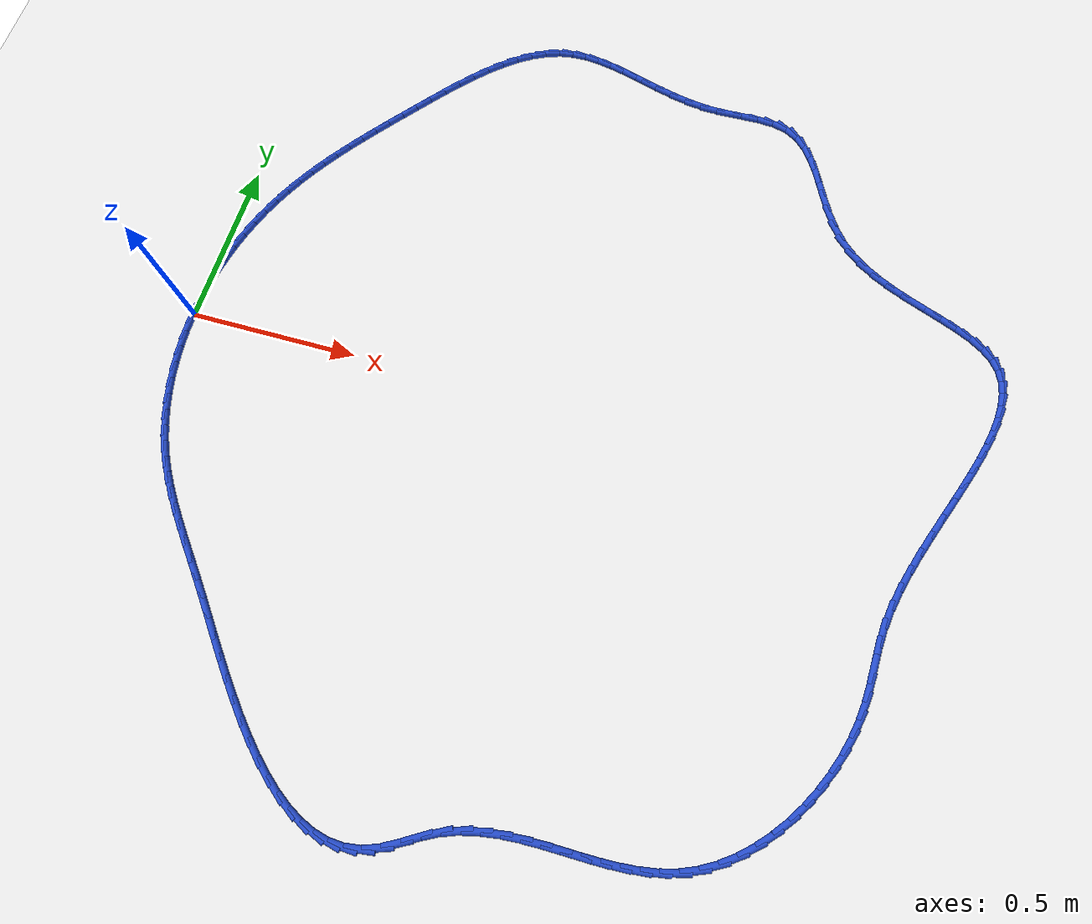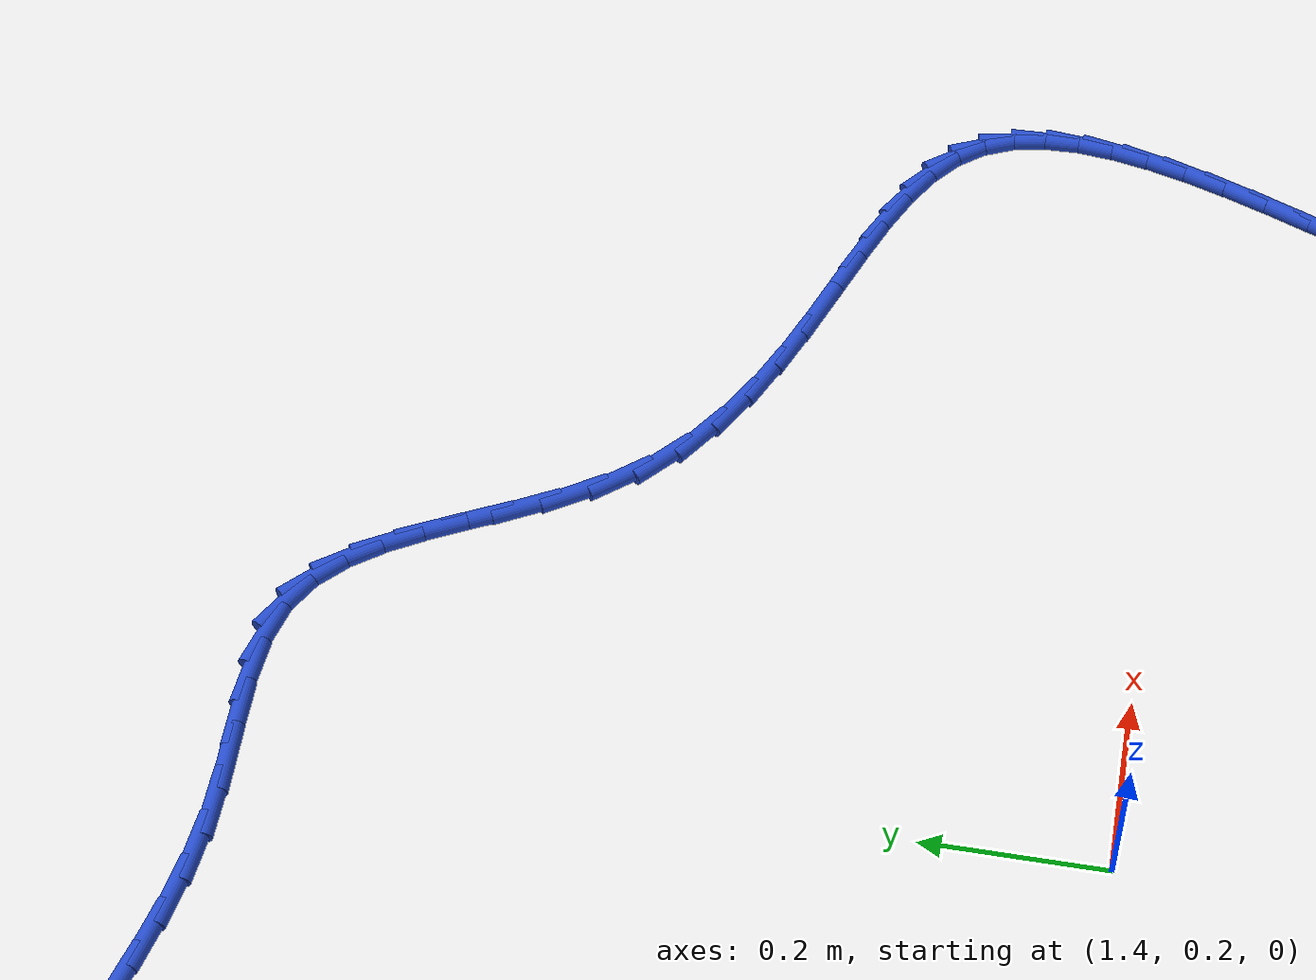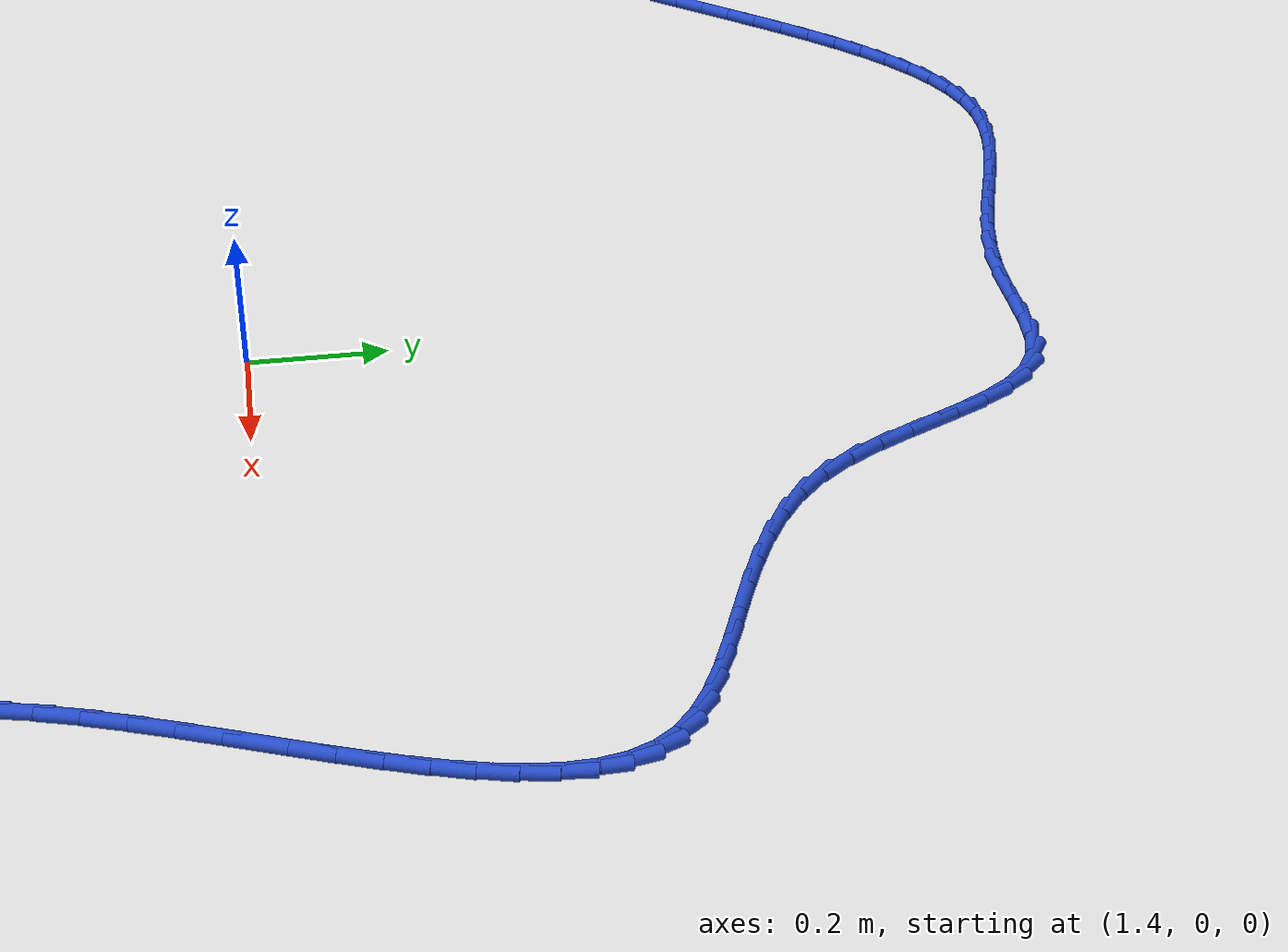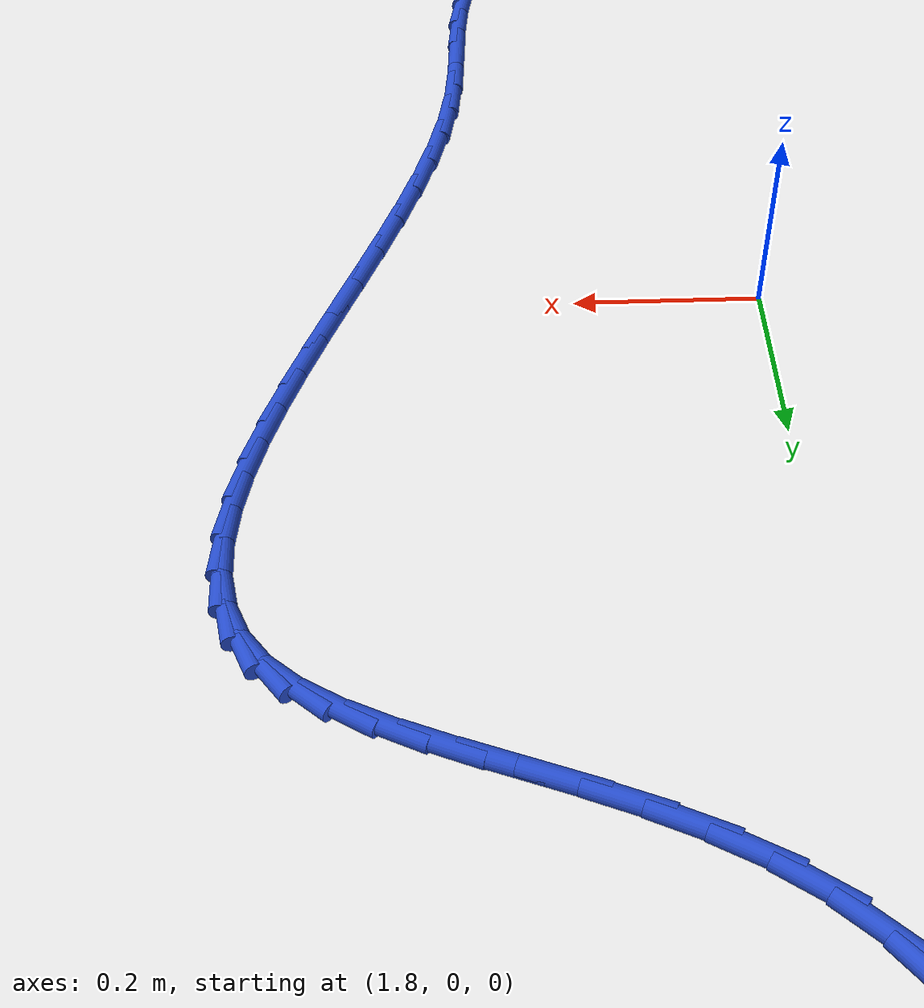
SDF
<sdf version="1.6">
 <world name="default">
  <light name="sun" type="directional">
   <pose>0 0 10 0 -0 0</pose>
   <diffuse>0.8 0.8 0.8 1</diffuse>
   <specular>0.2 0.2 0.2 1</specular>
   <attenuation>
    <range>1000</range>
    <constant>0.9</constant>
    <linear>0.01</linear>
    <quadratic>0.001</quadratic>
   </attenuation>
   <direction>-0.5 0.1 -0.9</direction>
  </light>
  <model name="ground_plane">
   <static>1</static>
   <link name="link">
    <collision name="collision">
     <geometry><plane><normal>0 0 1</normal><size>100 100</size></plane></geometry>
     <surface><friction><ode><mu>100</mu><mu2>50</mu2></ode></friction></surface>
    </collision>
    <visual name="visual">
     <cast_shadows>0</cast_shadows>
     <geometry><plane><normal>0 0 1</normal><size>100 100</size></plane></geometry>
     <material>
      <script><uri>file://media/materials/scripts/gazebo.material</uri><name>Gazebo/WhiteGlow</name></script>
     </material>
    </visual>
   </link>
  </model>
  <gravity>0 0 -9.8</gravity>
  <magnetic_field>6e-06 2.3e-05 -4.2e-05</magnetic_field>
  <atmosphere type="adiabatic"/>
  <physics name="default_physics" default="0" type="ode">
   <max_step_size>0.001</max_step_size>
   <real_time_factor>1</real_time_factor>
   <real_time_update_rate>1000</real_time_update_rate>
  </physics>
  <scene><ambient>0.4 0.4 0.4 1</ambient><background>0.7 0.7 0.7 1</background><shadows>1</shadows></scene>
  <spherical_coordinates>
   <surface_model>EARTH_WGS84</surface_model>
   <latitude_deg>0</latitude_deg>
   <longitude_deg>0</longitude_deg>
   <elevation>0</elevation>
   <heading_deg>0</heading_deg>
  </spherical_coordinates>
  <model name="line">
   <link name="link_0">
    <pose>3.122502256758253e-17 2.7755575615628914e-17 0.01 0 1.57 1.5381990420906606</pose>
    <collision name="collision">
     <geometry><cylinder><radius>0.01</radius><length>0.08</length></cylinder></geometry>
    </collision>
    <visual name="visual">
     <material>
      <script><name>Gazebo/Blue</name><uri>file://media/materials/scripts/gazebo.material</uri></script>
     </material>
     <geometry><cylinder><radius>0.01</radius><length>0.08</length></cylinder></geometry>
    </visual>
   </link>
   <link name="link_1">
    <pose>0.00164522733908944 0.05045342219584996 0.01 0 1.57 1.4889050247376745</pose>
    <collision name="collision">
     <geometry><cylinder><radius>0.01</radius><length>0.08</length></cylinder></geometry>
    </collision>
    <visual name="visual">
     <material>
      <script><name>Gazebo/Blue</name><uri>file://media/materials/scripts/gazebo.material</uri></script>
     </material>
     <geometry><cylinder><radius>0.01</radius><length>0.08</length></cylinder></geometry>
    </visual>
   </link>
   <link name="link_2">
    <pose>0.005759652638662704 0.10058357907015432 0.01 0 1.57 1.440484689456226</pose>
    <collision name="collision">
     <geometry><cylinder><radius>0.01</radius><length>0.08</length></cylinder></geometry>
    </collision>
    <visual name="visual">
     <material>
      <script><name>Gazebo/Blue</name><uri>file://media/materials/scripts/gazebo.material</uri></script>
     </material>
     <geometry><cylinder><radius>0.01</radius><length>0.08</length></cylinder></geometry>
    </visual>
   </link>
   <link name="link_3">
    <pose>0.01226964574504907 0.15025759481940254 0.01 0 1.57 1.3927698719391708</pose>
    <collision name="collision">
     <geometry><cylinder><radius>0.01</radius><length>0.08</length></cylinder></geometry>
    </collision>
    <visual name="visual">
     <material>
      <script><name>Gazebo/Blue</name><uri>file://media/materials/scripts/gazebo.material</uri></script>
     </material>
     <geometry><cylinder><radius>0.01</radius><length>0.08</length></cylinder></geometry>
    </visual>
   </link>
   <link name="link_4">
    <pose>0.021101576504577772 0.19934259364008408 0.01 0 1.57 1.3455779644179995</pose>
    <collision name="collision">
     <geometry><cylinder><radius>0.01</radius><length>0.08</length></cylinder></geometry>
    </collision>
    <visual name="visual">
     <material>
      <script><name>Gazebo/Blue</name><uri>file://media/materials/scripts/gazebo.material</uri></script>
     </material>
     <geometry><cylinder><radius>0.01</radius><length>0.08</length></cylinder></geometry>
    </visual>
   </link>
   <link name="link_5">
    <pose>0.03218181476357805 0.24770569972868833 0.01 0 1.57 1.298713417564979</pose>
    <collision name="collision">
     <geometry><cylinder><radius>0.01</radius><length>0.08</length></cylinder></geometry>
    </collision>
    <visual name="visual">
     <material>
      <script><name>Gazebo/Blue</name><uri>file://media/materials/scripts/gazebo.material</uri></script>
     </material>
     <geometry><cylinder><radius>0.01</radius><length>0.08</length></cylinder></geometry>
    </visual>
   </link>
   <link name="link_6">
    <pose>0.045436730368379155 0.2952140372817048 0.01 0 1.57 1.25196863100493</pose>
    <collision name="collision">
     <geometry><cylinder><radius>0.01</radius><length>0.08</length></cylinder></geometry>
    </collision>
    <visual name="visual">
     <material>
      <script><name>Gazebo/Blue</name><uri>file://media/materials/scripts/gazebo.material</uri></script>
     </material>
     <geometry><cylinder><radius>0.01</radius><length>0.08</length></cylinder></geometry>
    </visual>
   </link>
   <link name="link_7">
    <pose>0.060792693165310344 0.34173473049562303 0.01 0 1.57 1.2051243360913555</pose>
    <collision name="collision">
     <geometry><cylinder><radius>0.01</radius><length>0.08</length></cylinder></geometry>
    </collision>
    <visual name="visual">
     <material>
      <script><name>Gazebo/Blue</name><uri>file://media/materials/scripts/gazebo.material</uri></script>
     </material>
     <geometry><cylinder><radius>0.01</radius><length>0.08</length></cylinder></geometry>
    </visual>
   </link>
   <link name="link_8">
    <pose>0.07817607300070081 0.3871349035669322 0.01 0 1.57 1.158048484129779</pose>
    <collision name="collision">
     <geometry><cylinder><radius>0.01</radius><length>0.08</length></cylinder></geometry>
    </collision>
    <visual name="visual">
     <material>
      <script><name>Gazebo/Blue</name><uri>file://media/materials/scripts/gazebo.material</uri></script>
     </material>
     <geometry><cylinder><radius>0.01</radius><length>0.08</length></cylinder></geometry>
    </visual>
   </link>
   <link name="link_9">
    <pose>0.09751211679618497 0.4312909978084622 0.01 0 1.57 1.1124199148009029</pose>
    <collision name="collision">
     <geometry><cylinder><radius>0.01</radius><length>0.08</length></cylinder></geometry>
    </collision>
    <visual name="visual">
     <material>
      <script><name>Gazebo/Blue</name><uri>file://media/materials/scripts/gazebo.material</uri></script>
     </material>
     <geometry><cylinder><radius>0.01</radius><length>0.08</length></cylinder></geometry>
    </visual>
   </link>
   <link name="link_10">
    <pose>0.11870626003551571 0.47424383374070506 0.01 0 1.57 1.0701779051702192</pose>
    <collision name="collision">
     <geometry><cylinder><radius>0.01</radius><length>0.08</length></cylinder></geometry>
    </collision>
    <visual name="visual">
     <material>
      <script><name>Gazebo/Blue</name><uri>file://media/materials/scripts/gazebo.material</uri></script>
     </material>
     <geometry><cylinder><radius>0.01</radius><length>0.08</length></cylinder></geometry>
    </visual>
   </link>
   <link name="link_11">
    <pose>0.14164698502226902 0.5161748955927404 0.01 0 1.57 1.0318442887739931</pose>
    <collision name="collision">
     <geometry><cylinder><radius>0.01</radius><length>0.08</length></cylinder></geometry>
    </collision>
    <visual name="visual">
     <material>
      <script><name>Gazebo/Blue</name><uri>file://media/materials/scripts/gazebo.material</uri></script>
     </material>
     <geometry><cylinder><radius>0.01</radius><length>0.08</length></cylinder></geometry>
    </visual>
   </link>
   <link name="link_12">
    <pose>0.16622222714045012 0.5572702054876779 0.01 0 1.57 0.9977643349343708</pose>
    <collision name="collision">
     <geometry><cylinder><radius>0.01</radius><length>0.08</length></cylinder></geometry>
    </collision>
    <visual name="visual">
     <material>
      <script><name>Gazebo/Blue</name><uri>file://media/materials/scripts/gazebo.material</uri></script>
     </material>
     <geometry><cylinder><radius>0.01</radius><length>0.08</length></cylinder></geometry>
    </visual>
   </link>
   <link name="link_13">
    <pose>0.19231992177406415 0.5977157855486271 0.01 0 1.57 0.9681601267275276</pose>
    <collision name="collision">
     <geometry><cylinder><radius>0.01</radius><length>0.08</length></cylinder></geometry>
    </collision>
    <visual name="visual">
     <material>
      <script><name>Gazebo/Blue</name><uri>file://media/materials/scripts/gazebo.material</uri></script>
     </material>
     <geometry><cylinder><radius>0.01</radius><length>0.08</length></cylinder></geometry>
    </visual>
   </link>
   <link name="link_14">
    <pose>0.21982800430711644 0.6376976578986984 0.01 0 1.57 0.9431436747785589</pose>
    <collision name="collision">
     <geometry><cylinder><radius>0.01</radius><length>0.08</length></cylinder></geometry>
    </collision>
    <visual name="visual">
     <material>
      <script><name>Gazebo/Blue</name><uri>file://media/materials/scripts/gazebo.material</uri></script>
     </material>
     <geometry><cylinder><radius>0.01</radius><length>0.08</length></cylinder></geometry>
    </visual>
   </link>
   <link name="link_15">
    <pose>0.24863441012361204 0.6774018446610008 0.01 0 1.57 0.922734219279413</pose>
    <collision name="collision">
     <geometry><cylinder><radius>0.01</radius><length>0.08</length></cylinder></geometry>
    </collision>
    <visual name="visual">
     <material>
      <script><name>Gazebo/Blue</name><uri>file://media/materials/scripts/gazebo.material</uri></script>
     </material>
     <geometry><cylinder><radius>0.01</radius><length>0.08</length></cylinder></geometry>
    </visual>
   </link>
   <link name="link_16">
    <pose>0.27862707460755637 0.7170143679586447 0.01 0 1.57 0.9068765705767337</pose>
    <collision name="collision">
     <geometry><cylinder><radius>0.01</radius><length>0.08</length></cylinder></geometry>
    </collision>
    <visual name="visual">
     <material>
      <script><name>Gazebo/Blue</name><uri>file://media/materials/scripts/gazebo.material</uri></script>
     </material>
     <geometry><cylinder><radius>0.01</radius><length>0.08</length></cylinder></geometry>
    </visual>
   </link>
   <link name="link_17">
    <pose>0.30969393314295446 0.7567212499147394 0.01 0 1.57 0.8954582575250173</pose>
    <collision name="collision">
     <geometry><cylinder><radius>0.01</radius><length>0.08</length></cylinder></geometry>
    </collision>
    <visual name="visual">
     <material>
      <script><name>Gazebo/Blue</name><uri>file://media/materials/scripts/gazebo.material</uri></script>
     </material>
     <geometry><cylinder><radius>0.01</radius><length>0.08</length></cylinder></geometry>
    </visual>
   </link>
   <link name="link_18">
    <pose>0.3417229211138117 0.7967085126523951 0.01 0 1.57 0.8883241997426052</pose>
    <collision name="collision">
     <geometry><cylinder><radius>0.01</radius><length>0.08</length></cylinder></geometry>
    </collision>
    <visual name="visual">
     <material>
      <script><name>Gazebo/Blue</name><uri>file://media/materials/scripts/gazebo.material</uri></script>
     </material>
     <geometry><cylinder><radius>0.01</radius><length>0.08</length></cylinder></geometry>
    </visual>
   </link>
   <link name="link_19">
    <pose>0.37460197390413313 0.8371621782947213 0.01 0 1.57 0.8852015242344491</pose>
    <collision name="collision">
     <geometry><cylinder><radius>0.01</radius><length>0.08</length></cylinder></geometry>
    </collision>
    <visual name="visual">
     <material>
      <script><name>Gazebo/Blue</name><uri>file://media/materials/scripts/gazebo.material</uri></script>
     </material>
     <geometry><cylinder><radius>0.01</radius><length>0.08</length></cylinder></geometry>
    </visual>
   </link>
   <link name="link_20">
    <pose>0.4082200328626878 0.8782622125098972 0.01 0 1.57 0.8810524873996473</pose>
    <collision name="collision">
     <geometry><cylinder><radius>0.01</radius><length>0.08</length></cylinder></geometry>
    </collision>
    <visual name="visual">
     <material>
      <script><name>Gazebo/Blue</name><uri>file://media/materials/scripts/gazebo.material</uri></script>
     </material>
     <geometry><cylinder><radius>0.01</radius><length>0.08</length></cylinder></geometry>
    </visual>
   </link>
   <link name="link_21">
    <pose>0.44252290586661036 0.9198462135408749 0.01 0 1.57 0.868536293638658</pose>
    <collision name="collision">
     <geometry><cylinder><radius>0.01</radius><length>0.08</length></cylinder></geometry>
    </collision>
    <visual name="visual">
     <material>
      <script><name>Gazebo/Blue</name><uri>file://media/materials/scripts/gazebo.material</uri></script>
     </material>
     <geometry><cylinder><radius>0.01</radius><length>0.08</length></cylinder></geometry>
    </visual>
   </link>
   <link name="link_22">
    <pose>0.4775425929279206 0.9612328561066217 0.01 0 1.57 0.8468233029041009</pose>
    <collision name="collision">
     <geometry><cylinder><radius>0.01</radius><length>0.08</length></cylinder></geometry>
    </collision>
    <visual name="visual">
     <material>
      <script><name>Gazebo/Blue</name><uri>file://media/materials/scripts/gazebo.material</uri></script>
     </material>
     <geometry><cylinder><radius>0.01</radius><length>0.08</length></cylinder></geometry>
    </visual>
   </link>
   <link name="link_23">
    <pose>0.513318285007387 1.0016975215041508 0.01 0 1.57 0.8151971730808403</pose>
    <collision name="collision">
     <geometry><cylinder><radius>0.01</radius><length>0.08</length></cylinder></geometry>
    </collision>
    <visual name="visual">
     <material>
      <script><name>Gazebo/Blue</name><uri>file://media/materials/scripts/gazebo.material</uri></script>
     </material>
     <geometry><cylinder><radius>0.01</radius><length>0.08</length></cylinder></geometry>
    </visual>
   </link>
   <link name="link_24">
    <pose>0.5498891730657772 1.0405155910304742 0.01 0 1.57 0.7724213373083829</pose>
    <collision name="collision">
     <geometry><cylinder><radius>0.01</radius><length>0.08</length></cylinder></geometry>
    </collision>
    <visual name="visual">
     <material>
      <script><name>Gazebo/Blue</name><uri>file://media/materials/scripts/gazebo.material</uri></script>
     </material>
     <geometry><cylinder><radius>0.01</radius><length>0.08</length></cylinder></geometry>
    </visual>
   </link>
   <link name="link_25">
    <pose>0.5872944480638596 1.0769624459826037 0.01 0 1.57 0.7167106357839285</pose>
    <collision name="collision">
     <geometry><cylinder><radius>0.01</radius><length>0.08</length></cylinder></geometry>
    </collision>
    <visual name="visual">
     <material>
      <script><name>Gazebo/Blue</name><uri>file://media/materials/scripts/gazebo.material</uri></script>
     </material>
     <geometry><cylinder><radius>0.01</radius><length>0.08</length></cylinder></geometry>
    </visual>
   </link>
   <link name="link_26">
    <pose>0.6255733009624017 1.1103134676575528 0.01 0 1.57 0.6457321840138073</pose>
    <collision name="collision">
     <geometry><cylinder><radius>0.01</radius><length>0.08</length></cylinder></geometry>
    </collision>
    <visual name="visual">
     <material>
      <script><name>Gazebo/Blue</name><uri>file://media/materials/scripts/gazebo.material</uri></script>
     </material>
     <geometry><cylinder><radius>0.01</radius><length>0.08</length></cylinder></geometry>
    </visual>
   </link>
   <link name="link_27">
    <pose>0.6647649227221722 1.139844037352333 0.01 0 1.57 0.5567298702977895</pose>
    <collision name="collision">
     <geometry><cylinder><radius>0.01</radius><length>0.08</length></cylinder></geometry>
    </collision>
    <visual name="visual">
     <material>
      <script><name>Gazebo/Blue</name><uri>file://media/materials/scripts/gazebo.material</uri></script>
     </material>
     <geometry><cylinder><radius>0.01</radius><length>0.08</length></cylinder></geometry>
    </visual>
   </link>
   <link name="link_28">
    <pose>0.7049085043039387 1.164829536363957 0.01 0 1.57 0.44694956282326354</pose>
    <collision name="collision">
     <geometry><cylinder><radius>0.01</radius><length>0.08</length></cylinder></geometry>
    </collision>
    <visual name="visual">
     <material>
      <script><name>Gazebo/Blue</name><uri>file://media/materials/scripts/gazebo.material</uri></script>
     </material>
     <geometry><cylinder><radius>0.01</radius><length>0.08</length></cylinder></geometry>
    </visual>
   </link>
   <link name="link_29">
    <pose>0.7460432366684692 1.1845453459894366 0.01 0 1.57 0.3146147970580368</pose>
    <collision name="collision">
     <geometry><cylinder><radius>0.01</radius><length>0.08</length></cylinder></geometry>
    </collision>
    <visual name="visual">
     <material>
      <script><name>Gazebo/Blue</name><uri>file://media/materials/scripts/gazebo.material</uri></script>
     </material>
     <geometry><cylinder><radius>0.01</radius><length>0.08</length></cylinder></geometry>
    </visual>
   </link>
   <link name="link_30">
    <pose>0.7882083107765319 1.198266847525785 0.01 0 1.57 0.16151394588122622</pose>
    <collision name="collision">
     <geometry><cylinder><radius>0.01</radius><length>0.08</length></cylinder></geometry>
    </collision>
    <visual name="visual">
     <material>
      <script><name>Gazebo/Blue</name><uri>file://media/materials/scripts/gazebo.material</uri></script>
     </material>
     <geometry><cylinder><radius>0.01</radius><length>0.08</length></cylinder></geometry>
    </visual>
   </link>
   <link name="link_31">
    <pose>0.8314415455578255 1.2053109774898916 0.01 0 1.57 0.013582639021974452</pose>
    <collision name="collision">
     <geometry><cylinder><radius>0.01</radius><length>0.08</length></cylinder></geometry>
    </collision>
    <visual name="visual">
     <material>
      <script><name>Gazebo/Blue</name><uri>file://media/materials/scripts/gazebo.material</uri></script>
     </material>
     <geometry><cylinder><radius>0.01</radius><length>0.08</length></cylinder></geometry>
    </visual>
   </link>
   <link name="link_32">
    <pose>0.8757504445424328 1.2059128462832558 0.01 0 1.57 -0.10340564429680514</pose>
    <collision name="collision">
     <geometry><cylinder><radius>0.01</radius><length>0.08</length></cylinder></geometry>
    </collision>
    <visual name="visual">
     <material>
      <script><name>Gazebo/Blue</name><uri>file://media/materials/scripts/gazebo.material</uri></script>
     </material>
     <geometry><cylinder><radius>0.01</radius><length>0.08</length></cylinder></geometry>
    </visual>
   </link>
   <link name="link_33">
    <pose>0.9211128698527231 1.2012053247463066 0.01 0 1.57 -0.18842717048367777</pose>
    <collision name="collision">
     <geometry><cylinder><radius>0.01</radius><length>0.08</length></cylinder></geometry>
    </collision>
    <visual name="visual">
     <material>
      <script><name>Gazebo/Blue</name><uri>file://media/materials/scripts/gazebo.material</uri></script>
     </material>
     <geometry><cylinder><radius>0.01</radius><length>0.08</length></cylinder></geometry>
    </visual>
   </link>
   <link name="link_34">
    <pose>0.9675054463997397 1.1923587556032322 0.01 0 1.57 -0.2442922288382279</pose>
    <collision name="collision">
     <geometry><cylinder><radius>0.01</radius><length>0.08</length></cylinder></geometry>
    </collision>
    <visual name="visual">
     <material>
      <script><name>Gazebo/Blue</name><uri>file://media/materials/scripts/gazebo.material</uri></script>
     </material>
     <geometry><cylinder><radius>0.01</radius><length>0.08</length></cylinder></geometry>
    </visual>
   </link>
   <link name="link_35">
    <pose>1.0149047990945237 1.180543481578219 0.01 0 1.57 -0.27428211320257284</pose>
    <collision name="collision">
     <geometry><cylinder><radius>0.01</radius><length>0.08</length></cylinder></geometry>
    </collision>
    <visual name="visual">
     <material>
      <script><name>Gazebo/Blue</name><uri>file://media/materials/scripts/gazebo.material</uri></script>
     </material>
     <geometry><cylinder><radius>0.01</radius><length>0.08</length></cylinder></geometry>
    </visual>
   </link>
   <link name="link_36">
    <pose>1.0632875528481183 1.1669298453954553 0.01 0 1.57 -0.2809904153653087</pose>
    <collision name="collision">
     <geometry><cylinder><radius>0.01</radius><length>0.08</length></cylinder></geometry>
    </collision>
    <visual name="visual">
     <material>
      <script><name>Gazebo/Blue</name><uri>file://media/materials/scripts/gazebo.material</uri></script>
     </material>
     <geometry><cylinder><radius>0.01</radius><length>0.08</length></cylinder></geometry>
    </visual>
   </link>
   <link name="link_37">
    <pose>1.1126303325715656 1.152688189779128 0.01 0 1.57 -0.26600694118107526</pose>
    <collision name="collision">
     <geometry><cylinder><radius>0.01</radius><length>0.08</length></cylinder></geometry>
    </collision>
    <visual name="visual">
     <material>
      <script><name>Gazebo/Blue</name><uri>file://media/materials/scripts/gazebo.material</uri></script>
     </material>
     <geometry><cylinder><radius>0.01</radius><length>0.08</length></cylinder></geometry>
    </visual>
   </link>
   <link name="link_38">
    <pose>1.1629097631759078 1.1389888574534244 0.01 0 1.57 -0.23000433167421203</pose>
    <collision name="collision">
     <geometry><cylinder><radius>0.01</radius><length>0.08</length></cylinder></geometry>
    </collision>
    <visual name="visual">
     <material>
      <script><name>Gazebo/Blue</name><uri>file://media/materials/scripts/gazebo.material</uri></script>
     </material>
     <geometry><cylinder><radius>0.01</radius><length>0.08</length></cylinder></geometry>
    </visual>
   </link>
   <link name="link_39">
    <pose>1.2141024695721871 1.1270021911425323 0.01 0 1.57 -0.1730444830334125</pose>
    <collision name="collision">
     <geometry><cylinder><radius>0.01</radius><length>0.08</length></cylinder></geometry>
    </collision>
    <visual name="visual">
     <material>
      <script><name>Gazebo/Blue</name><uri>file://media/materials/scripts/gazebo.material</uri></script>
     </material>
     <geometry><cylinder><radius>0.01</radius><length>0.08</length></cylinder></geometry>
    </visual>
   </link>
   <link name="link_40">
    <pose>1.266185076671446 1.117898533570639 0.01 0 1.57 -0.09509266738395368</pose>
    <collision name="collision">
     <geometry><cylinder><radius>0.01</radius><length>0.08</length></cylinder></geometry>
    </collision>
    <visual name="visual">
     <material>
      <script><name>Gazebo/Blue</name><uri>file://media/materials/scripts/gazebo.material</uri></script>
     </material>
     <geometry><cylinder><radius>0.01</radius><length>0.08</length></cylinder></geometry>
    </visual>
   </link>
   <link name="link_41">
    <pose>1.319134209384727 1.1128482274619316 0.01 0 1.57 -0.009628564560574142</pose>
    <collision name="collision">
     <geometry><cylinder><radius>0.01</radius><length>0.08</length></cylinder></geometry>
    </collision>
    <visual name="visual">
     <material>
      <script><name>Gazebo/Blue</name><uri>file://media/materials/scripts/gazebo.material</uri></script>
     </material>
     <geometry><cylinder><radius>0.01</radius><length>0.08</length></cylinder></geometry>
    </visual>
   </link>
   <link name="link_42">
    <pose>1.3726979488487137 1.1123324695997892 0.01 0 1.57 0.030185073726526394</pose>
    <collision name="collision">
     <geometry><cylinder><radius>0.01</radius><length>0.08</length></cylinder></geometry>
    </collision>
    <visual name="visual">
     <material>
      <script><name>Gazebo/Blue</name><uri>file://media/materials/scripts/gazebo.material</uri></script>
     </material>
     <geometry><cylinder><radius>0.01</radius><length>0.08</length></cylinder></geometry>
    </visual>
   </link>
   <link name="link_43">
    <pose>1.4256623854616461 1.1139316907574226 0.01 0 1.57 0.01044259917137673</pose>
    <collision name="collision">
     <geometry><cylinder><radius>0.01</radius><length>0.08</length></cylinder></geometry>
    </collision>
    <visual name="visual">
     <material>
      <script><name>Gazebo/Blue</name><uri>file://media/materials/scripts/gazebo.material</uri></script>
     </material>
     <geometry><cylinder><radius>0.01</radius><length>0.08</length></cylinder></geometry>
    </visual>
   </link>
   <link name="link_44">
    <pose>1.4765605393496686 1.1144632190978578 0.01 0 1.57 -0.07835395242602636</pose>
    <collision name="collision">
     <geometry><cylinder><radius>0.01</radius><length>0.08</length></cylinder></geometry>
    </collision>
    <visual name="visual">
     <material>
      <script><name>Gazebo/Blue</name><uri>file://media/materials/scripts/gazebo.material</uri></script>
     </material>
     <geometry><cylinder><radius>0.01</radius><length>0.08</length></cylinder></geometry>
    </visual>
   </link>
   <link name="link_45">
    <pose>1.5239254294586493 1.110744379225144 0.01 0 1.57 -0.257396400774457</pose>
    <collision name="collision">
     <geometry><cylinder><radius>0.01</radius><length>0.08</length></cylinder></geometry>
    </collision>
    <visual name="visual">
     <material>
      <script><name>Gazebo/Blue</name><uri>file://media/materials/scripts/gazebo.material</uri></script>
     </material>
     <geometry><cylinder><radius>0.01</radius><length>0.08</length></cylinder></geometry>
    </visual>
   </link>
   <link name="link_46">
    <pose>1.5662900747344575 1.0995924957433307 0.01 0 1.57 -0.5290875430586806</pose>
    <collision name="collision">
     <geometry><cylinder><radius>0.01</radius><length>0.08</length></cylinder></geometry>
    </collision>
    <visual name="visual">
     <material>
      <script><name>Gazebo/Blue</name><uri>file://media/materials/scripts/gazebo.material</uri></script>
     </material>
     <geometry><cylinder><radius>0.01</radius><length>0.08</length></cylinder></geometry>
    </visual>
   </link>
   <link name="link_47">
    <pose>1.602518867879516 1.0784098114921703 0.01 0 1.57 -0.7791425349269764</pose>
    <collision name="collision">
     <geometry><cylinder><radius>0.01</radius><length>0.08</length></cylinder></geometry>
    </collision>
    <visual name="visual">
     <material>
      <script><name>Gazebo/Blue</name><uri>file://media/materials/scripts/gazebo.material</uri></script>
     </material>
     <geometry><cylinder><radius>0.01</radius><length>0.08</length></cylinder></geometry>
    </visual>
   </link>
   <link name="link_48">
    <pose>1.633370326514422 1.0479419487535897 0.01 0 1.57 -0.9524889581873364</pose>
    <collision name="collision">
     <geometry><cylinder><radius>0.01</radius><length>0.08</length></cylinder></geometry>
    </collision>
    <visual name="visual">
     <material>
      <script><name>Gazebo/Blue</name><uri>file://media/materials/scripts/gazebo.material</uri></script>
     </material>
     <geometry><cylinder><radius>0.01</radius><length>0.08</length></cylinder></geometry>
    </visual>
   </link>
   <link name="link_49">
    <pose>1.660274862442041 1.0101205113542149 0.01 0 1.57 -1.0572623724471997</pose>
    <collision name="collision">
     <geometry><cylinder><radius>0.01</radius><length>0.08</length></cylinder></geometry>
    </collision>
    <visual name="visual">
     <material>
      <script><name>Gazebo/Blue</name><uri>file://media/materials/scripts/gazebo.material</uri></script>
     </material>
     <geometry><cylinder><radius>0.01</radius><length>0.08</length></cylinder></geometry>
    </visual>
   </link>
   <link name="link_50">
    <pose>1.6846636819597736 0.9668785055079543 0.01 0 1.57 -1.1081845661702687</pose>
    <collision name="collision">
     <geometry><cylinder><radius>0.01</radius><length>0.08</length></cylinder></geometry>
    </collision>
    <visual name="visual">
     <material>
      <script><name>Gazebo/Blue</name><uri>file://media/materials/scripts/gazebo.material</uri></script>
     </material>
     <geometry><cylinder><radius>0.01</radius><length>0.08</length></cylinder></geometry>
    </visual>
   </link>
   <link name="link_51">
    <pose>1.7079679913650208 0.920148937428717 0.01 0 1.57 -1.1153178840445754</pose>
    <collision name="collision">
     <geometry><cylinder><radius>0.01</radius><length>0.08</length></cylinder></geometry>
    </collision>
    <visual name="visual">
     <material>
      <script><name>Gazebo/Blue</name><uri>file://media/materials/scripts/gazebo.material</uri></script>
     </material>
     <geometry><cylinder><radius>0.01</radius><length>0.08</length></cylinder></geometry>
    </visual>
   </link>
   <link name="link_52">
    <pose>1.7316189969551823 0.8718648133304107 0.01 0 1.57 -1.0828040066533071</pose>
    <collision name="collision">
     <geometry><cylinder><radius>0.01</radius><length>0.08</length></cylinder></geometry>
    </collision>
    <visual name="visual">
     <material>
      <script><name>Gazebo/Blue</name><uri>file://media/materials/scripts/gazebo.material</uri></script>
     </material>
     <geometry><cylinder><radius>0.01</radius><length>0.08</length></cylinder></geometry>
    </visual>
   </link>
   <link name="link_53">
    <pose>1.7570479050276584 0.8239591394269435 0.01 0 1.57 -1.0099663603229205</pose>
    <collision name="collision">
     <geometry><cylinder><radius>0.01</radius><length>0.08</length></cylinder></geometry>
    </collision>
    <visual name="visual">
     <material>
      <script><name>Gazebo/Blue</name><uri>file://media/materials/scripts/gazebo.material</uri></script>
     </material>
     <geometry><cylinder><radius>0.01</radius><length>0.08</length></cylinder></geometry>
    </visual>
   </link>
   <link name="link_54">
    <pose>1.7856859218798506 0.7783649219322237 0.01 0 1.57 -0.8931356048850871</pose>
    <collision name="collision">
     <geometry><cylinder><radius>0.01</radius><length>0.08</length></cylinder></geometry>
    </collision>
    <visual name="visual">
     <material>
      <script><name>Gazebo/Blue</name><uri>file://media/materials/scripts/gazebo.material</uri></script>
     </material>
     <geometry><cylinder><radius>0.01</radius><length>0.08</length></cylinder></geometry>
    </visual>
   </link>
   <link name="link_55">
    <pose>1.818964219756859 0.7370151309387891 0.01 0 1.57 -0.743382730152277</pose>
    <collision name="collision">
     <geometry><cylinder><radius>0.01</radius><length>0.08</length></cylinder></geometry>
    </collision>
    <visual name="visual">
     <material>
      <script><name>Gazebo/Blue</name><uri>file://media/materials/scripts/gazebo.material</uri></script>
     </material>
     <geometry><cylinder><radius>0.01</radius><length>0.08</length></cylinder></geometry>
    </visual>
   </link>
   <link name="link_56">
    <pose>1.85780777952394 0.7013057881630441 0.01 0 1.57 -0.6119482674964225</pose>
    <collision name="collision">
     <geometry><cylinder><radius>0.01</radius><length>0.08</length></cylinder></geometry>
    </collision>
    <visual name="visual">
     <material>
      <script><name>Gazebo/Blue</name><uri>file://media/materials/scripts/gazebo.material</uri></script>
     </material>
     <geometry><cylinder><radius>0.01</radius><length>0.08</length></cylinder></geometry>
    </visual>
   </link>
   <link name="link_57">
    <pose>1.90135816501194 0.6707411350210538 0.01 0 1.57 -0.5106284547234087</pose>
    <collision name="collision">
     <geometry><cylinder><radius>0.01</radius><length>0.08</length></cylinder></geometry>
    </collision>
    <visual name="visual">
     <material>
      <script><name>Gazebo/Blue</name><uri>file://media/materials/scripts/gazebo.material</uri></script>
     </material>
     <geometry><cylinder><radius>0.01</radius><length>0.08</length></cylinder></geometry>
    </visual>
   </link>
   <link name="link_58">
    <pose>1.9483643805030402 0.644409000835389 0.01 0 1.57 -0.437404965082955</pose>
    <collision name="collision">
     <geometry><cylinder><radius>0.01</radius><length>0.08</length></cylinder></geometry>
    </collision>
    <visual name="visual">
     <material>
      <script><name>Gazebo/Blue</name><uri>file://media/materials/scripts/gazebo.material</uri></script>
     </material>
     <geometry><cylinder><radius>0.01</radius><length>0.08</length></cylinder></geometry>
    </visual>
   </link>
   <link name="link_59">
    <pose>1.9975754302794226 0.6213972149286205 0.01 0 1.57 -0.38971150550244243</pose>
    <collision name="collision">
     <geometry><cylinder><radius>0.01</radius><length>0.08</length></cylinder></geometry>
    </collision>
    <visual name="visual">
     <material>
      <script><name>Gazebo/Blue</name><uri>file://media/materials/scripts/gazebo.material</uri></script>
     </material>
     <geometry><cylinder><radius>0.01</radius><length>0.08</length></cylinder></geometry>
    </visual>
   </link>
   <link name="link_60">
    <pose>2.047740318623269 0.6007936066233189 0.01 0 1.57 -0.3659103031381147</pose>
    <collision name="collision">
     <geometry><cylinder><radius>0.01</radius><length>0.08</length></cylinder></geometry>
    </collision>
    <visual name="visual">
     <material>
      <script><name>Gazebo/Blue</name><uri>file://media/materials/scripts/gazebo.material</uri></script>
     </material>
     <geometry><cylinder><radius>0.01</radius><length>0.08</length></cylinder></geometry>
    </visual>
   </link>
   <link name="link_61">
    <pose>2.0976080498167615 0.5816860052420548 0.01 0 1.57 -0.366079253160277</pose>
    <collision name="collision">
     <geometry><cylinder><radius>0.01</radius><length>0.08</length></cylinder></geometry>
    </collision>
    <visual name="visual">
     <material>
      <script><name>Gazebo/Blue</name><uri>file://media/materials/scripts/gazebo.material</uri></script>
     </material>
     <geometry><cylinder><radius>0.01</radius><length>0.08</length></cylinder></geometry>
    </visual>
   </link>
   <link name="link_62">
    <pose>2.1459276281420827 0.5631622401073987 0.01 0 1.57 -0.3926413310451618</pose>
    <collision name="collision">
     <geometry><cylinder><radius>0.01</radius><length>0.08</length></cylinder></geometry>
    </collision>
    <visual name="visual">
     <material>
      <script><name>Gazebo/Blue</name><uri>file://media/materials/scripts/gazebo.material</uri></script>
     </material>
     <geometry><cylinder><radius>0.01</radius><length>0.08</length></cylinder></geometry>
    </visual>
   </link>
   <link name="link_63">
    <pose>2.1914480578814124 0.5443101405419213 0.01 0 1.57 -0.45117580609698726</pose>
    <collision name="collision">
     <geometry><cylinder><radius>0.01</radius><length>0.08</length></cylinder></geometry>
    </collision>
    <visual name="visual">
     <material>
      <script><name>Gazebo/Blue</name><uri>file://media/materials/scripts/gazebo.material</uri></script>
     </material>
     <geometry><cylinder><radius>0.01</radius><length>0.08</length></cylinder></geometry>
    </visual>
   </link>
   <link name="link_64">
    <pose>2.2329183433169337 0.5242175358681931 0.01 0 1.57 -0.5514011608680375</pose>
    <collision name="collision">
     <geometry><cylinder><radius>0.01</radius><length>0.08</length></cylinder></geometry>
    </collision>
    <visual name="visual">
     <material>
      <script><name>Gazebo/Blue</name><uri>file://media/materials/scripts/gazebo.material</uri></script>
     </material>
     <geometry><cylinder><radius>0.01</radius><length>0.08</length></cylinder></geometry>
    </visual>
   </link>
   <link name="link_65">
    <pose>2.269087488730829 0.501972255408785 0.01 0 1.57 -0.7071474329540973</pose>
    <collision name="collision">
     <geometry><cylinder><radius>0.01</radius><length>0.08</length></cylinder></geometry>
    </collision>
    <visual name="visual">
     <material>
      <script><name>Gazebo/Blue</name><uri>file://media/materials/scripts/gazebo.material</uri></script>
     </material>
     <geometry><cylinder><radius>0.01</radius><length>0.08</length></cylinder></geometry>
    </visual>
   </link>
   <link name="link_66">
    <pose>2.298704498405279 0.47666212848626743 0.01 0 1.57 -0.9266036395273842</pose>
    <collision name="collision">
     <geometry><cylinder><radius>0.01</radius><length>0.08</length></cylinder></geometry>
    </collision>
    <visual name="visual">
     <material>
      <script><name>Gazebo/Blue</name><uri>file://media/materials/scripts/gazebo.material</uri></script>
     </material>
     <geometry><cylinder><radius>0.01</radius><length>0.08</length></cylinder></geometry>
    </visual>
   </link>
   <link name="link_67">
    <pose>2.320642708490921 0.44745328731373224 0.01 0 1.57 -1.1634513760108935</pose>
    <collision name="collision">
     <geometry><cylinder><radius>0.01</radius><length>0.08</length></cylinder></geometry>
    </collision>
    <visual name="visual">
     <material>
      <script><name>Gazebo/Blue</name><uri>file://media/materials/scripts/gazebo.material</uri></script>
     </material>
     <geometry><cylinder><radius>0.01</radius><length>0.08</length></cylinder></geometry>
    </visual>
   </link>
   <link name="link_68">
    <pose>2.3349645647713837 0.4142607527244456 0.01 0 1.57 -1.3718431645962288</pose>
    <collision name="collision">
     <geometry><cylinder><radius>0.01</radius><length>0.08</length></cylinder></geometry>
    </collision>
    <visual name="visual">
     <material>
      <script><name>Gazebo/Blue</name><uri>file://media/materials/scripts/gazebo.material</uri></script>
     </material>
     <geometry><cylinder><radius>0.01</radius><length>0.08</length></cylinder></geometry>
    </visual>
   </link>
   <link name="link_69">
    <pose>2.342393281423511 0.37741569046928014 0.01 0 1.57 -1.5392874166045165</pose>
    <collision name="collision">
     <geometry><cylinder><radius>0.01</radius><length>0.08</length></cylinder></geometry>
    </collision>
    <visual name="visual">
     <material>
      <script><name>Gazebo/Blue</name><uri>file://media/materials/scripts/gazebo.material</uri></script>
     </material>
     <geometry><cylinder><radius>0.01</radius><length>0.08</length></cylinder></geometry>
    </visual>
   </link>
   <link name="link_70">
    <pose>2.343659159987838 0.337253729845503 0.01 0 1.57 1.4745175910899624</pose>
    <collision name="collision">
     <geometry><cylinder><radius>0.01</radius><length>0.08</length></cylinder></geometry>
    </collision>
    <visual name="visual">
     <material>
      <script><name>Gazebo/Blue</name><uri>file://media/materials/scripts/gazebo.material</uri></script>
     </material>
     <geometry><cylinder><radius>0.01</radius><length>0.08</length></cylinder></geometry>
    </visual>
   </link>
   <link name="link_71">
    <pose>2.339492502004898 0.2941105001503811 0.01 0 1.57 1.3794743848728883</pose>
    <collision name="collision">
     <geometry><cylinder><radius>0.01</radius><length>0.08</length></cylinder></geometry>
    </collision>
    <visual name="visual">
     <material>
      <script><name>Gazebo/Blue</name><uri>file://media/materials/scripts/gazebo.material</uri></script>
     </material>
     <geometry><cylinder><radius>0.01</radius><length>0.08</length></cylinder></geometry>
    </visual>
   </link>
   <link name="link_72">
    <pose>2.3306236090152246 0.24832163068118232 0.01 0 1.57 1.3099133139320436</pose>
    <collision name="collision">
     <geometry><cylinder><radius>0.01</radius><length>0.08</length></cylinder></geometry>
    </collision>
    <visual name="visual">
     <material>
      <script><name>Gazebo/Blue</name><uri>file://media/materials/scripts/gazebo.material</uri></script>
     </material>
     <geometry><cylinder><radius>0.01</radius><length>0.08</length></cylinder></geometry>
    </visual>
   </link>
   <link name="link_73">
    <pose>2.317782782559352 0.2002227507351733 0.01 0 1.57 1.260024653978424</pose>
    <collision name="collision">
     <geometry><cylinder><radius>0.01</radius><length>0.08</length></cylinder></geometry>
    </collision>
    <visual name="visual">
     <material>
      <script><name>Gazebo/Blue</name><uri>file://media/materials/scripts/gazebo.material</uri></script>
     </material>
     <geometry><cylinder><radius>0.01</radius><length>0.08</length></cylinder></geometry>
    </visual>
   </link>
   <link name="link_74">
    <pose>2.301700324177814 0.15014948960962127 0.01 0 1.57 1.2256265970006008</pose>
    <collision name="collision">
     <geometry><cylinder><radius>0.01</radius><length>0.08</length></cylinder></geometry>
    </collision>
    <visual name="visual">
     <material>
      <script><name>Gazebo/Blue</name><uri>file://media/materials/scripts/gazebo.material</uri></script>
     </material>
     <geometry><cylinder><radius>0.01</radius><length>0.08</length></cylinder></geometry>
    </visual>
   </link>
   <link name="link_75">
    <pose>2.2831065354111453 0.09843747660179335 0.01 0 1.57 1.2038791691177222</pose>
    <collision name="collision">
     <geometry><cylinder><radius>0.01</radius><length>0.08</length></cylinder></geometry>
    </collision>
    <visual name="visual">
     <material>
      <script><name>Gazebo/Blue</name><uri>file://media/materials/scripts/gazebo.material</uri></script>
     </material>
     <geometry><cylinder><radius>0.01</radius><length>0.08</length></cylinder></geometry>
    </visual>
   </link>
   <link name="link_76">
    <pose>2.262731717799879 0.045422341008956195 0.01 0 1.57 1.192967785224151</pose>
    <collision name="collision">
     <geometry><cylinder><radius>0.01</radius><length>0.08</length></cylinder></geometry>
    </collision>
    <visual name="visual">
     <material>
      <script><name>Gazebo/Blue</name><uri>file://media/materials/scripts/gazebo.material</uri></script>
     </material>
     <geometry><cylinder><radius>0.01</radius><length>0.08</length></cylinder></geometry>
    </visual>
   </link>
   <link name="link_77">
    <pose>2.241306172884549 -0.008560287871622496 0.01 0 1.57 1.1918666649581073</pose>
    <collision name="collision">
     <geometry><cylinder><radius>0.01</radius><length>0.08</length></cylinder></geometry>
    </collision>
    <visual name="visual">
     <material>
      <script><name>Gazebo/Blue</name><uri>file://media/materials/scripts/gazebo.material</uri></script>
     </material>
     <geometry><cylinder><radius>0.01</radius><length>0.08</length></cylinder></geometry>
    </visual>
   </link>
   <link name="link_78">
    <pose>2.2195602022056904 -0.06317478074267474 0.01 0 1.57 1.20019102868321</pose>
    <collision name="collision">
     <geometry><cylinder><radius>0.01</radius><length>0.08</length></cylinder></geometry>
    </collision>
    <visual name="visual">
     <material>
      <script><name>Gazebo/Blue</name><uri>file://media/materials/scripts/gazebo.material</uri></script>
     </material>
     <geometry><cylinder><radius>0.01</radius><length>0.08</length></cylinder></geometry>
    </visual>
   </link>
   <link name="link_79">
    <pose>2.1982241073038358 -0.11808550830693519 0.01 0 1.57 1.2181242834997617</pose>
    <collision name="collision">
     <geometry><cylinder><radius>0.01</radius><length>0.08</length></cylinder></geometry>
    </collision>
    <visual name="visual">
     <material>
      <script><name>Gazebo/Blue</name><uri>file://media/materials/scripts/gazebo.material</uri></script>
     </material>
     <geometry><cylinder><radius>0.01</radius><length>0.08</length></cylinder></geometry>
    </visual>
   </link>
   <link name="link_80">
    <pose>2.1780281897195204 -0.17295684126713484 0.01 0 1.57 1.2464056839638447</pose>
    <collision name="collision">
     <geometry><cylinder><radius>0.01</radius><length>0.08</length></cylinder></geometry>
    </collision>
    <visual name="visual">
     <material>
      <script><name>Gazebo/Blue</name><uri>file://media/materials/scripts/gazebo.material</uri></script>
     </material>
     <geometry><cylinder><radius>0.01</radius><length>0.08</length></cylinder></geometry>
    </visual>
   </link>
   <link name="link_81">
    <pose>2.1597027509932767 -0.2274531503260085 0.01 0 1.57 1.2863653479555297</pose>
    <collision name="collision">
     <geometry><cylinder><radius>0.01</radius><length>0.08</length></cylinder></geometry>
    </collision>
    <visual name="visual">
     <material>
      <script><name>Gazebo/Blue</name><uri>file://media/materials/scripts/gazebo.material</uri></script>
     </material>
     <geometry><cylinder><radius>0.01</radius><length>0.08</length></cylinder></geometry>
    </visual>
   </link>
   <link name="link_82">
    <pose>2.1439780926656398 -0.28123880618628805 0.01 0 1.57 1.339987535237432</pose>
    <collision name="collision">
     <geometry><cylinder><radius>0.01</radius><length>0.08</length></cylinder></geometry>
    </collision>
    <visual name="visual">
     <material>
      <script><name>Gazebo/Blue</name><uri>file://media/materials/scripts/gazebo.material</uri></script>
     </material>
     <geometry><cylinder><radius>0.01</radius><length>0.08</length></cylinder></geometry>
    </visual>
   </link>
   <link name="link_83">
    <pose>2.1315845162771434 -0.3339781795507053 0.01 0 1.57 1.4098290516328773</pose>
    <collision name="collision">
     <geometry><cylinder><radius>0.01</radius><length>0.08</length></cylinder></geometry>
    </collision>
    <visual name="visual">
     <material>
      <script><name>Gazebo/Blue</name><uri>file://media/materials/scripts/gazebo.material</uri></script>
     </material>
     <geometry><cylinder><radius>0.01</radius><length>0.08</length></cylinder></geometry>
    </visual>
   </link>
   <link name="link_84">
    <pose>2.123245128609718 -0.38533791795775985 0.01 0 1.57 1.482183946385227</pose>
    <collision name="collision">
     <geometry><cylinder><radius>0.01</radius><length>0.08</length></cylinder></geometry>
    </collision>
    <visual name="visual">
     <material>
      <script><name>Gazebo/Blue</name><uri>file://media/materials/scripts/gazebo.material</uri></script>
     </material>
     <geometry><cylinder><radius>0.01</radius><length>0.08</length></cylinder></geometry>
    </visual>
   </link>
   <link name="link_85">
    <pose>2.118809706570921 -0.4352610407885325 0.01 0 1.57 1.5222443048338958</pose>
    <collision name="collision">
     <geometry><cylinder><radius>0.01</radius><length>0.08</length></cylinder></geometry>
    </collision>
    <visual name="visual">
     <material>
      <script><name>Gazebo/Blue</name><uri>file://media/materials/scripts/gazebo.material</uri></script>
     </material>
     <geometry><cylinder><radius>0.01</radius><length>0.08</length></cylinder></geometry>
    </visual>
   </link>
   <link name="link_86">
    <pose>2.1164304018336697 -0.48422779376650826 0.01 0 1.57 1.522098049754579</pose>
    <collision name="collision">
     <geometry><cylinder><radius>0.01</radius><length>0.08</length></cylinder></geometry>
    </collision>
    <visual name="visual">
     <material>
      <script><name>Gazebo/Blue</name><uri>file://media/materials/scripts/gazebo.material</uri></script>
     </material>
     <geometry><cylinder><radius>0.01</radius><length>0.08</length></cylinder></geometry>
    </visual>
   </link>
   <link name="link_87">
    <pose>2.114064111839739 -0.5327802122930629 0.01 0 1.57 1.480729098906891</pose>
    <collision name="collision">
     <geometry><cylinder><radius>0.01</radius><length>0.08</length></cylinder></geometry>
    </collision>
    <visual name="visual">
     <material>
      <script><name>Gazebo/Blue</name><uri>file://media/materials/scripts/gazebo.material</uri></script>
     </material>
     <geometry><cylinder><radius>0.01</radius><length>0.08</length></cylinder></geometry>
    </visual>
   </link>
   <link name="link_88">
    <pose>2.1096677340309107 -0.5814603317695725 0.01 0 1.57 1.4047521994074639</pose>
    <collision name="collision">
     <geometry><cylinder><radius>0.01</radius><length>0.08</length></cylinder></geometry>
    </collision>
    <visual name="visual">
     <material>
      <script><name>Gazebo/Blue</name><uri>file://media/materials/scripts/gazebo.material</uri></script>
     </material>
     <geometry><cylinder><radius>0.01</radius><length>0.08</length></cylinder></geometry>
    </visual>
   </link>
   <link name="link_89">
    <pose>2.1014147101652836 -0.6307064998414816 0.01 0 1.57 1.3239006424480826</pose>
    <collision name="collision">
     <geometry><cylinder><radius>0.01</radius><length>0.08</length></cylinder></geometry>
    </collision>
    <visual name="visual">
     <material>
      <script><name>Gazebo/Blue</name><uri>file://media/materials/scripts/gazebo.material</uri></script>
     </material>
     <geometry><cylinder><radius>0.01</radius><length>0.08</length></cylinder></geometry>
    </visual>
   </link>
   <link name="link_90">
    <pose>2.0889241334458566 -0.6802648439347093 0.01 0 1.57 1.2477209170124883</pose>
    <collision name="collision">
     <geometry><cylinder><radius>0.01</radius><length>0.08</length></cylinder></geometry>
    </collision>
    <visual name="visual">
     <material>
      <script><name>Gazebo/Blue</name><uri>file://media/materials/scripts/gazebo.material</uri></script>
     </material>
     <geometry><cylinder><radius>0.01</radius><length>0.08</length></cylinder></geometry>
    </visual>
   </link>
   <link name="link_91">
    <pose>2.072407084244984 -0.7295980306936878 0.01 0 1.57 1.1743708725592843</pose>
    <collision name="collision">
     <geometry><cylinder><radius>0.01</radius><length>0.08</length></cylinder></geometry>
    </collision>
    <visual name="visual">
     <material>
      <script><name>Gazebo/Blue</name><uri>file://media/materials/scripts/gazebo.material</uri></script>
     </material>
     <geometry><cylinder><radius>0.01</radius><length>0.08</length></cylinder></geometry>
    </visual>
   </link>
   <link name="link_92">
    <pose>2.052076425852334 -0.778167873049863 0.01 0 1.57 1.1021305476242402</pose>
    <collision name="collision">
     <geometry><cylinder><radius>0.01</radius><length>0.08</length></cylinder></geometry>
    </collision>
    <visual name="visual">
     <material>
      <script><name>Gazebo/Blue</name><uri>file://media/materials/scripts/gazebo.material</uri></script>
     </material>
     <geometry><cylinder><radius>0.01</radius><length>0.08</length></cylinder></geometry>
    </visual>
   </link>
   <link name="link_93">
    <pose>2.0281450215575743 -0.8254361839346764 0.01 0 1.57 1.0293717907103082</pose>
    <collision name="collision">
     <geometry><cylinder><radius>0.01</radius><length>0.08</length></cylinder></geometry>
    </collision>
    <visual name="visual">
     <material>
      <script><name>Gazebo/Blue</name><uri>file://media/materials/scripts/gazebo.material</uri></script>
     </material>
     <geometry><cylinder><radius>0.01</radius><length>0.08</length></cylinder></geometry>
    </visual>
   </link>
   <link name="link_94">
    <pose>2.0008257346503764 -0.8708647762795747 0.01 0 1.57 0.9544983098817302</pose>
    <collision name="collision">
     <geometry><cylinder><radius>0.01</radius><length>0.08</length></cylinder></geometry>
    </collision>
    <visual name="visual">
     <material>
      <script><name>Gazebo/Blue</name><uri>file://media/materials/scripts/gazebo.material</uri></script>
     </material>
     <geometry><cylinder><radius>0.01</radius><length>0.08</length></cylinder></geometry>
    </visual>
   </link>
   <link name="link_95">
    <pose>1.970331428420409 -0.9139154630160006 0.01 0 1.57 0.8758968035671769</pose>
    <collision name="collision">
     <geometry><cylinder><radius>0.01</radius><length>0.08</length></cylinder></geometry>
    </collision>
    <visual name="visual">
     <material>
      <script><name>Gazebo/Blue</name><uri>file://media/materials/scripts/gazebo.material</uri></script>
     </material>
     <geometry><cylinder><radius>0.01</radius><length>0.08</length></cylinder></geometry>
    </visual>
   </link>
   <link name="link_96">
    <pose>1.936874966157343 -0.9540500570753977 0.01 0 1.57 0.7919090454624175</pose>
    <collision name="collision">
     <geometry><cylinder><radius>0.01</radius><length>0.08</length></cylinder></geometry>
    </collision>
    <visual name="visual">
     <material>
      <script><name>Gazebo/Blue</name><uri>file://media/materials/scripts/gazebo.material</uri></script>
     </material>
     <geometry><cylinder><radius>0.01</radius><length>0.08</length></cylinder></geometry>
    </visual>
   </link>
   <link name="link_97">
    <pose>1.900669211150846 -0.990730371389211 0.01 0 1.57 0.7008412805455088</pose>
    <collision name="collision">
     <geometry><cylinder><radius>0.01</radius><length>0.08</length></cylinder></geometry>
    </collision>
    <visual name="visual">
     <material>
      <script><name>Gazebo/Blue</name><uri>file://media/materials/scripts/gazebo.material</uri></script>
     </material>
     <geometry><cylinder><radius>0.01</radius><length>0.08</length></cylinder></geometry>
    </visual>
   </link>
   <link name="link_98">
    <pose>1.8619270266905887 -1.0234182188888838 0.01 0 1.57 0.6010376751209414</pose>
    <collision name="collision">
     <geometry><cylinder><radius>0.01</radius><length>0.08</length></cylinder></geometry>
    </collision>
    <visual name="visual">
     <material>
      <script><name>Gazebo/Blue</name><uri>file://media/materials/scripts/gazebo.material</uri></script>
     </material>
     <geometry><cylinder><radius>0.01</radius><length>0.08</length></cylinder></geometry>
    </visual>
   </link>
   <link name="link_99">
    <pose>1.8208612760662402 -1.051575412505861 0.01 0 1.57 0.4910550107025136</pose>
    <collision name="collision">
     <geometry><cylinder><radius>0.01</radius><length>0.08</length></cylinder></geometry>
    </collision>
    <visual name="visual">
     <material>
      <script><name>Gazebo/Blue</name><uri>file://media/materials/scripts/gazebo.material</uri></script>
     </material>
     <geometry><cylinder><radius>0.01</radius><length>0.08</length></cylinder></geometry>
    </visual>
   </link>
   <link name="link_100">
    <pose>1.777684822567469 -1.0746637651715858 0.01 0 1.57 0.3705531998053798</pose>
    <collision name="collision">
     <geometry><cylinder><radius>0.01</radius><length>0.08</length></cylinder></geometry>
    </collision>
    <visual name="visual">
     <material>
      <script><name>Gazebo/Blue</name><uri>file://media/materials/scripts/gazebo.material</uri></script>
     </material>
     <geometry><cylinder><radius>0.01</radius><length>0.08</length></cylinder></geometry>
    </visual>
   </link>
   <link name="link_101">
    <pose>1.7326118944667959 -1.0921745851313203 0.01 0 1.57 0.2542248696266358</pose>
    <collision name="collision">
     <geometry><cylinder><radius>0.01</radius><length>0.08</length></cylinder></geometry>
    </collision>
    <visual name="visual">
     <material>
      <script><name>Gazebo/Blue</name><uri>file://media/materials/scripts/gazebo.material</uri></script>
     </material>
     <geometry><cylinder><radius>0.01</radius><length>0.08</length></cylinder></geometry>
    </visual>
   </link>
   <link name="link_102">
    <pose>1.685889854719128 -1.1043151734035148 0.01 0 1.57 0.15907775691857928</pose>
    <collision name="collision">
     <geometry><cylinder><radius>0.01</radius><length>0.08</length></cylinder></geometry>
    </collision>
    <visual name="visual">
     <material>
      <script><name>Gazebo/Blue</name><uri>file://media/materials/scripts/gazebo.material</uri></script>
     </material>
     <geometry><cylinder><radius>0.01</radius><length>0.08</length></cylinder></geometry>
    </visual>
   </link>
   <link name="link_103">
    <pose>1.6378001975087586 -1.1120303577252149 0.01 0 1.57 0.08658479463529188</pose>
    <collision name="collision">
     <geometry><cylinder><radius>0.01</radius><length>0.08</length></cylinder></geometry>
    </collision>
    <visual name="visual">
     <material>
      <script><name>Gazebo/Blue</name><uri>file://media/materials/scripts/gazebo.material</uri></script>
     </material>
     <geometry><cylinder><radius>0.01</radius><length>0.08</length></cylinder></geometry>
    </visual>
   </link>
   <link name="link_104">
    <pose>1.588625981367087 -1.1162987691218793 0.01 0 1.57 0.036007315588917545</pose>
    <collision name="collision">
     <geometry><cylinder><radius>0.01</radius><length>0.08</length></cylinder></geometry>
    </collision>
    <visual name="visual">
     <material>
      <script><name>Gazebo/Blue</name><uri>file://media/materials/scripts/gazebo.material</uri></script>
     </material>
     <geometry><cylinder><radius>0.01</radius><length>0.08</length></cylinder></geometry>
    </visual>
   </link>
   <link name="link_105">
    <pose>1.538650264825513 -1.1180990386189673 0.01 0 1.57 0.006154270304015762</pose>
    <collision name="collision">
     <geometry><cylinder><radius>0.01</radius><length>0.08</length></cylinder></geometry>
    </collision>
    <visual name="visual">
     <material>
      <script><name>Gazebo/Blue</name><uri>file://media/materials/scripts/gazebo.material</uri></script>
     </material>
     <geometry><cylinder><radius>0.01</radius><length>0.08</length></cylinder></geometry>
    </visual>
   </link>
   <link name="link_106">
    <pose>1.4881561064154383 -1.1184097972419387 0.01 0 1.57 -0.003944845167351985</pose>
    <collision name="collision">
     <geometry><cylinder><radius>0.01</radius><length>0.08</length></cylinder></geometry>
    </collision>
    <visual name="visual">
     <material>
      <script><name>Gazebo/Blue</name><uri>file://media/materials/scripts/gazebo.material</uri></script>
     </material>
     <geometry><cylinder><radius>0.01</radius><length>0.08</length></cylinder></geometry>
    </visual>
   </link>
   <link name="link_107">
    <pose>1.437426564668261 -1.1182096760162519 0.01 0 1.57 0.005280536842371491</pose>
    <collision name="collision">
     <geometry><cylinder><radius>0.01</radius><length>0.08</length></cylinder></geometry>
    </collision>
    <visual name="visual">
     <material>
      <script><name>Gazebo/Blue</name><uri>file://media/materials/scripts/gazebo.material</uri></script>
     </material>
     <geometry><cylinder><radius>0.01</radius><length>0.08</length></cylinder></geometry>
    </visual>
   </link>
   <link name="link_108">
    <pose>1.386744698115383 -1.1184773059673665 0.01 0 1.57 0.03402804366277655</pose>
    <collision name="collision">
     <geometry><cylinder><radius>0.01</radius><length>0.08</length></cylinder></geometry>
    </collision>
    <visual name="visual">
     <material>
      <script><name>Gazebo/Blue</name><uri>file://media/materials/scripts/gazebo.material</uri></script>
     </material>
     <geometry><cylinder><radius>0.01</radius><length>0.08</length></cylinder></geometry>
    </visual>
   </link>
   <link name="link_109">
    <pose>1.3363935652882053 -1.1201913181207421 0.01 0 1.57 0.08302636087835184</pose>
    <collision name="collision">
     <geometry><cylinder><radius>0.01</radius><length>0.08</length></cylinder></geometry>
    </collision>
    <visual name="visual">
     <material>
      <script><name>Gazebo/Blue</name><uri>file://media/materials/scripts/gazebo.material</uri></script>
     </material>
     <geometry><cylinder><radius>0.01</radius><length>0.08</length></cylinder></geometry>
    </visual>
   </link>
   <link name="link_110">
    <pose>1.286656224718126 -1.1243303435018375 0.01 0 1.57 0.1532242805654047</pose>
    <collision name="collision">
     <geometry><cylinder><radius>0.01</radius><length>0.08</length></cylinder></geometry>
    </collision>
    <visual name="visual">
     <material>
      <script><name>Gazebo/Blue</name><uri>file://media/materials/scripts/gazebo.material</uri></script>
     </material>
     <geometry><cylinder><radius>0.01</radius><length>0.08</length></cylinder></geometry>
    </visual>
   </link>
   <link name="link_111">
    <pose>1.2378157349365464 -1.1318730131361119 0.01 0 1.57 0.24517217509011993</pose>
    <collision name="collision">
     <geometry><cylinder><radius>0.01</radius><length>0.08</length></cylinder></geometry>
    </collision>
    <visual name="visual">
     <material>
      <script><name>Gazebo/Blue</name><uri>file://media/materials/scripts/gazebo.material</uri></script>
     </material>
     <geometry><cylinder><radius>0.01</radius><length>0.08</length></cylinder></geometry>
    </visual>
   </link>
   <link name="link_112">
    <pose>1.190155154474868 -1.1437979580490243 0.01 0 1.57 0.358044519066353</pose>
    <collision name="collision">
     <geometry><cylinder><radius>0.01</radius><length>0.08</length></cylinder></geometry>
    </collision>
    <visual name="visual">
     <material>
      <script><name>Gazebo/Blue</name><uri>file://media/materials/scripts/gazebo.material</uri></script>
     </material>
     <geometry><cylinder><radius>0.01</radius><length>0.08</length></cylinder></geometry>
    </visual>
   </link>
   <link name="link_113">
    <pose>1.1439575418644892 -1.1610838092660347 0.01 0 1.57 0.4796557169158955</pose>
    <collision name="collision">
     <geometry><cylinder><radius>0.01</radius><length>0.08</length></cylinder></geometry>
    </collision>
    <visual name="visual">
     <material>
      <script><name>Gazebo/Blue</name><uri>file://media/materials/scripts/gazebo.material</uri></script>
     </material>
     <geometry><cylinder><radius>0.01</radius><length>0.08</length></cylinder></geometry>
    </visual>
   </link>
   <link name="link_114">
    <pose>1.099440027462613 -1.1842406328208421 0.01 0 1.57 0.5342414280984414</pose>
    <collision name="collision">
     <geometry><cylinder><radius>0.01</radius><length>0.08</length></cylinder></geometry>
    </collision>
    <visual name="visual">
     <material>
      <script><name>Gazebo/Blue</name><uri>file://media/materials/scripts/gazebo.material</uri></script>
     </material>
     <geometry><cylinder><radius>0.01</radius><length>0.08</length></cylinder></geometry>
    </visual>
   </link>
   <link name="link_115">
    <pose>1.0562582960511524 -1.2097881864373645 0.01 0 1.57 0.4860495044604346</pose>
    <collision name="collision">
     <geometry><cylinder><radius>0.01</radius><length>0.08</length></cylinder></geometry>
    </collision>
    <visual name="visual">
     <material>
      <script><name>Gazebo/Blue</name><uri>file://media/materials/scripts/gazebo.material</uri></script>
     </material>
     <geometry><cylinder><radius>0.01</radius><length>0.08</length></cylinder></geometry>
    </visual>
   </link>
   <link name="link_116">
    <pose>1.0137841100801717 -1.2322283338708155 0.01 0 1.57 0.3298990707841623</pose>
    <collision name="collision">
     <geometry><cylinder><radius>0.01</radius><length>0.08</length></cylinder></geometry>
    </collision>
    <visual name="visual">
     <material>
      <script><name>Gazebo/Blue</name><uri>file://media/materials/scripts/gazebo.material</uri></script>
     </material>
     <geometry><cylinder><radius>0.01</radius><length>0.08</length></cylinder></geometry>
    </visual>
   </link>
   <link name="link_117">
    <pose>0.9714612073601118 -1.2467202079059008 0.01 0 1.57 0.13467146576200703</pose>
    <collision name="collision">
     <geometry><cylinder><radius>0.01</radius><length>0.08</length></cylinder></geometry>
    </collision>
    <visual name="visual">
     <material>
      <script><name>Gazebo/Blue</name><uri>file://media/materials/scripts/gazebo.material</uri></script>
     </material>
     <geometry><cylinder><radius>0.01</radius><length>0.08</length></cylinder></geometry>
    </visual>
   </link>
   <link name="link_118">
    <pose>0.9291771576716209 -1.252449340090266 0.01 0 1.57 -0.05580429475518159</pose>
    <collision name="collision">
     <geometry><cylinder><radius>0.01</radius><length>0.08</length></cylinder></geometry>
    </collision>
    <visual name="visual">
     <material>
      <script><name>Gazebo/Blue</name><uri>file://media/materials/scripts/gazebo.material</uri></script>
     </material>
     <geometry><cylinder><radius>0.01</radius><length>0.08</length></cylinder></geometry>
    </visual>
   </link>
   <link name="link_119">
    <pose>0.8869838916973921 -1.250092327458204 0.01 0 1.57 -0.22815823633447668</pose>
    <collision name="collision">
     <geometry><cylinder><radius>0.01</radius><length>0.08</length></cylinder></geometry>
    </collision>
    <visual name="visual">
     <material>
      <script><name>Gazebo/Blue</name><uri>file://media/materials/scripts/gazebo.material</uri></script>
     </material>
     <geometry><cylinder><radius>0.01</radius><length>0.08</length></cylinder></geometry>
    </visual>
   </link>
   <link name="link_120">
    <pose>0.8449336071915946 -1.2403281898894662 0.01 0 1.57 -0.3753508156830387</pose>
    <collision name="collision">
     <geometry><cylinder><radius>0.01</radius><length>0.08</length></cylinder></geometry>
    </collision>
    <visual name="visual">
     <material>
      <script><name>Gazebo/Blue</name><uri>file://media/materials/scripts/gazebo.material</uri></script>
     </material>
     <geometry><cylinder><radius>0.01</radius><length>0.08</length></cylinder></geometry>
    </visual>
   </link>
   <link name="link_121">
    <pose>0.8030785019083989 -1.2238359472638038 0.01 0 1.57 -0.4964935165476492</pose>
    <collision name="collision">
     <geometry><cylinder><radius>0.01</radius><length>0.08</length></cylinder></geometry>
    </collision>
    <visual name="visual">
     <material>
      <script><name>Gazebo/Blue</name><uri>file://media/materials/scripts/gazebo.material</uri></script>
     </material>
     <geometry><cylinder><radius>0.01</radius><length>0.08</length></cylinder></geometry>
    </visual>
   </link>
   <link name="link_122">
    <pose>0.7614707736019766 -1.2012946194609684 0.01 0 1.57 -0.5942216570076018</pose>
    <collision name="collision">
     <geometry><cylinder><radius>0.01</radius><length>0.08</length></cylinder></geometry>
    </collision>
    <visual name="visual">
     <material>
      <script><name>Gazebo/Blue</name><uri>file://media/materials/scripts/gazebo.material</uri></script>
     </material>
     <geometry><cylinder><radius>0.01</radius><length>0.08</length></cylinder></geometry>
    </visual>
   </link>
   <link name="link_123">
    <pose>0.7201626200264968 -1.1733832263607116 0.01 0 1.57 -0.6723144791762253</pose>
    <collision name="collision">
     <geometry><cylinder><radius>0.01</radius><length>0.08</length></cylinder></geometry>
    </collision>
    <visual name="visual">
     <material>
      <script><name>Gazebo/Blue</name><uri>file://media/materials/scripts/gazebo.material</uri></script>
     </material>
     <geometry><cylinder><radius>0.01</radius><length>0.08</length></cylinder></geometry>
    </visual>
   </link>
   <link name="link_124">
    <pose>0.6792062389361302 -1.1407807878427845 0.01 0 1.57 -0.7344108232550602</pose>
    <collision name="collision">
     <geometry><cylinder><radius>0.01</radius><length>0.08</length></cylinder></geometry>
    </collision>
    <visual name="visual">
     <material>
      <script><name>Gazebo/Blue</name><uri>file://media/materials/scripts/gazebo.material</uri></script>
     </material>
     <geometry><cylinder><radius>0.01</radius><length>0.08</length></cylinder></geometry>
    </visual>
   </link>
   <link name="link_125">
    <pose>0.6386538280850479 -1.104166323786939 0.01 0 1.57 -0.7835395168214674</pose>
    <collision name="collision">
     <geometry><cylinder><radius>0.01</radius><length>0.08</length></cylinder></geometry>
    </collision>
    <visual name="visual">
     <material>
      <script><name>Gazebo/Blue</name><uri>file://media/materials/scripts/gazebo.material</uri></script>
     </material>
     <geometry><cylinder><radius>0.01</radius><length>0.08</length></cylinder></geometry>
    </visual>
   </link>
   <link name="link_126">
    <pose>0.5985575852274196 -1.0642188540729265 0.01 0 1.57 -0.8220480408588032</pose>
    <collision name="collision">
     <geometry><cylinder><radius>0.01</radius><length>0.08</length></cylinder></geometry>
    </collision>
    <visual name="visual">
     <material>
      <script><name>Gazebo/Blue</name><uri>file://media/materials/scripts/gazebo.material</uri></script>
     </material>
     <geometry><cylinder><radius>0.01</radius><length>0.08</length></cylinder></geometry>
    </visual>
   </link>
   <link name="link_127">
    <pose>0.5589697081174163 -1.0216173985804986 0.01 0 1.57 -0.8516748721481268</pose>
    <collision name="collision">
     <geometry><cylinder><radius>0.01</radius><length>0.08</length></cylinder></geometry>
    </collision>
    <visual name="visual">
     <material>
      <script><name>Gazebo/Blue</name><uri>file://media/materials/scripts/gazebo.material</uri></script>
     </material>
     <geometry><cylinder><radius>0.01</radius><length>0.08</length></cylinder></geometry>
    </visual>
   </link>
   <link name="link_128">
    <pose>0.5199423945092074 -0.9770409771894056 0.01 0 1.57 -0.8736496232288888</pose>
    <collision name="collision">
     <geometry><cylinder><radius>0.01</radius><length>0.08</length></cylinder></geometry>
    </collision>
    <visual name="visual">
     <material>
      <script><name>Gazebo/Blue</name><uri>file://media/materials/scripts/gazebo.material</uri></script>
     </material>
     <geometry><cylinder><radius>0.01</radius><length>0.08</length></cylinder></geometry>
    </visual>
   </link>
   <link name="link_129">
    <pose>0.48152784215696404 -0.9311686097794002 0.01 0 1.57 -0.8887773019427171</pose>
    <collision name="collision">
     <geometry><cylinder><radius>0.01</radius><length>0.08</length></cylinder></geometry>
    </collision>
    <visual name="visual">
     <material>
      <script><name>Gazebo/Blue</name><uri>file://media/materials/scripts/gazebo.material</uri></script>
     </material>
     <geometry><cylinder><radius>0.01</radius><length>0.08</length></cylinder></geometry>
    </visual>
   </link>
   <link name="link_130">
    <pose>0.4437782488148571 -0.8846793162302341 0.01 0 1.57 -0.8974928423899609</pose>
    <collision name="collision">
     <geometry><cylinder><radius>0.01</radius><length>0.08</length></cylinder></geometry>
    </collision>
    <visual name="visual">
     <material>
      <script><name>Gazebo/Blue</name><uri>file://media/materials/scripts/gazebo.material</uri></script>
     </material>
     <geometry><cylinder><radius>0.01</radius><length>0.08</length></cylinder></geometry>
    </visual>
   </link>
   <link name="link_131">
    <pose>0.4067458122370559 -0.8382521164216576 0.01 0 1.57 -0.8998813375744895</pose>
    <collision name="collision">
     <geometry><cylinder><radius>0.01</radius><length>0.08</length></cylinder></geometry>
    </collision>
    <visual name="visual">
     <material>
      <script><name>Gazebo/Blue</name><uri>file://media/materials/scripts/gazebo.material</uri></script>
     </material>
     <geometry><cylinder><radius>0.01</radius><length>0.08</length></cylinder></geometry>
    </visual>
   </link>
   <link name="link_132">
    <pose>0.3704827301777321 -0.7925660302334238 0.01 0 1.57 -0.8956592407972229</pose>
    <collision name="collision">
     <geometry><cylinder><radius>0.01</radius><length>0.08</length></cylinder></geometry>
    </collision>
    <visual name="visual">
     <material>
      <script><name>Gazebo/Blue</name><uri>file://media/materials/scripts/gazebo.material</uri></script>
     </material>
     <geometry><cylinder><radius>0.01</radius><length>0.08</length></cylinder></geometry>
    </visual>
   </link>
   <link name="link_133">
    <pose>0.3350412003910548 -0.7483000775452822 0.01 0 1.57 -0.8858889709633269</pose>
    <collision name="collision">
     <geometry><cylinder><radius>0.01</radius><length>0.08</length></cylinder></geometry>
    </collision>
    <visual name="visual">
     <material>
      <script><name>Gazebo/Blue</name><uri>file://media/materials/scripts/gazebo.material</uri></script>
     </material>
     <geometry><cylinder><radius>0.01</radius><length>0.08</length></cylinder></geometry>
    </visual>
   </link>
   <link name="link_134">
    <pose>0.3004889277154117 -0.7059986078162992 0.01 0 1.57 -0.8804124587141177</pose>
    <collision name="collision">
     <geometry><cylinder><radius>0.01</radius><length>0.08</length></cylinder></geometry>
    </collision>
    <visual name="visual">
     <material>
      <script><name>Gazebo/Blue</name><uri>file://media/materials/scripts/gazebo.material</uri></script>
     </material>
     <geometry><cylinder><radius>0.01</radius><length>0.08</length></cylinder></geometry>
    </visual>
   </link>
   <link name="link_135">
    <pose>0.2669826057260676 -0.6654331527105176 0.01 0 1.57 -0.8836918130532102</pose>
    <collision name="collision">
     <geometry><cylinder><radius>0.01</radius><length>0.08</length></cylinder></geometry>
    </collision>
    <visual name="visual">
     <material>
      <script><name>Gazebo/Blue</name><uri>file://media/materials/scripts/gazebo.material</uri></script>
     </material>
     <geometry><cylinder><radius>0.01</radius><length>0.08</length></cylinder></geometry>
    </visual>
   </link>
   <link name="link_136">
    <pose>0.23471061254481124 -0.6261000811889044 0.01 0 1.57 -0.8966001584998707</pose>
    <collision name="collision">
     <geometry><cylinder><radius>0.01</radius><length>0.08</length></cylinder></geometry>
    </collision>
    <visual name="visual">
     <material>
      <script><name>Gazebo/Blue</name><uri>file://media/materials/scripts/gazebo.material</uri></script>
     </material>
     <geometry><cylinder><radius>0.01</radius><length>0.08</length></cylinder></geometry>
    </visual>
   </link>
   <link name="link_137">
    <pose>0.2038613648682217 -0.5874954272117973 0.01 0 1.57 -0.9197851140580959</pose>
    <collision name="collision">
     <geometry><cylinder><radius>0.01</radius><length>0.08</length></cylinder></geometry>
    </collision>
    <visual name="visual">
     <material>
      <script><name>Gazebo/Blue</name><uri>file://media/materials/scripts/gazebo.material</uri></script>
     </material>
     <geometry><cylinder><radius>0.01</radius><length>0.08</length></cylinder></geometry>
    </visual>
   </link>
   <link name="link_138">
    <pose>0.17462327939287778 -0.5491152247395343 0.01 0 1.57 -0.9535605815452589</pose>
    <collision name="collision">
     <geometry><cylinder><radius>0.01</radius><length>0.08</length></cylinder></geometry>
    </collision>
    <visual name="visual">
     <material>
      <script><name>Gazebo/Blue</name><uri>file://media/materials/scripts/gazebo.material</uri></script>
     </material>
     <geometry><cylinder><radius>0.01</radius><length>0.08</length></cylinder></geometry>
    </visual>
   </link>
   <link name="link_139">
    <pose>0.14718477281535686 -0.5104555077324515 0.01 0 1.57 -0.9977713481135946</pose>
    <collision name="collision">
     <geometry><cylinder><radius>0.01</radius><length>0.08</length></cylinder></geometry>
    </collision>
    <visual name="visual">
     <material>
      <script><name>Gazebo/Blue</name><uri>file://media/materials/scripts/gazebo.material</uri></script>
     </material>
     <geometry><cylinder><radius>0.01</radius><length>0.08</length></cylinder></geometry>
    </visual>
   </link>
   <link name="link_140">
    <pose>0.12173426183223833 -0.4710123101508873 0.01 0 1.57 -1.0516604870746398</pose>
    <collision name="collision">
     <geometry><cylinder><radius>0.01</radius><length>0.08</length></cylinder></geometry>
    </collision>
    <visual name="visual">
     <material>
      <script><name>Gazebo/Blue</name><uri>file://media/materials/scripts/gazebo.material</uri></script>
     </material>
     <geometry><cylinder><radius>0.01</radius><length>0.08</length></cylinder></geometry>
    </visual>
   </link>
   <link name="link_141">
    <pose>0.09846016314009975 -0.4302816659551776 0.01 0 1.57 -1.1136376845189633</pose>
    <collision name="collision">
     <geometry><cylinder><radius>0.01</radius><length>0.08</length></cylinder></geometry>
    </collision>
    <visual name="visual">
     <material>
      <script><name>Gazebo/Blue</name><uri>file://media/materials/scripts/gazebo.material</uri></script>
     </material>
     <geometry><cylinder><radius>0.01</radius><length>0.08</length></cylinder></geometry>
    </visual>
   </link>
   <link name="link_142">
    <pose>0.07754833459355764 -0.387770597233515 0.01 0 1.57 -1.1774489280026847</pose>
    <collision name="collision">
     <geometry><cylinder><radius>0.01</radius><length>0.08</length></cylinder></geometry>
    </collision>
    <visual name="visual">
     <material>
      <script><name>Gazebo/Blue</name><uri>file://media/materials/scripts/gazebo.material</uri></script>
     </material>
     <geometry><cylinder><radius>0.01</radius><length>0.08</length></cylinder></geometry>
    </visual>
   </link>
   <link name="link_143">
    <pose>0.059105316152696666 -0.3433267313866304 0.01 0 1.57 -1.2377081715111673</pose>
    <collision name="collision">
     <geometry><cylinder><radius>0.01</radius><length>0.08</length></cylinder></geometry>
    </collision>
    <visual name="visual">
     <material>
      <script><name>Gazebo/Blue</name><uri>file://media/materials/scripts/gazebo.material</uri></script>
     </material>
     <geometry><cylinder><radius>0.01</radius><length>0.08</length></cylinder></geometry>
    </visual>
   </link>
   <link name="link_144">
    <pose>0.04314495711284013 -0.29719572620960916 0.01 0 1.57 -1.2947650112117015</pose>
    <collision name="collision">
     <geometry><cylinder><radius>0.01</radius><length>0.08</length></cylinder></geometry>
    </collision>
    <visual name="visual">
     <material>
      <script><name>Gazebo/Blue</name><uri>file://media/materials/scripts/gazebo.material</uri></script>
     </material>
     <geometry><cylinder><radius>0.01</radius><length>0.08</length></cylinder></geometry>
    </visual>
   </link>
   <link name="link_145">
    <pose>0.029675853004438545 -0.24964580010933463 0.01 0 1.57 -1.3492549448311562</pose>
    <collision name="collision">
     <geometry><cylinder><radius>0.01</radius><length>0.08</length></cylinder></geometry>
    </collision>
    <visual name="visual">
     <material>
      <script><name>Gazebo/Blue</name><uri>file://media/materials/scripts/gazebo.material</uri></script>
     </material>
     <geometry><cylinder><radius>0.01</radius><length>0.08</length></cylinder></geometry>
    </visual>
   </link>
   <link name="link_146">
    <pose>0.01870659935794145 -0.20094517149268662 0.01 0 1.57 -1.4017852839882752</pose>
    <collision name="collision">
     <geometry><cylinder><radius>0.01</radius><length>0.08</length></cylinder></geometry>
    </collision>
    <visual name="visual">
     <material>
      <script><name>Gazebo/Blue</name><uri>file://media/materials/scripts/gazebo.material</uri></script>
     </material>
     <geometry><cylinder><radius>0.01</radius><length>0.08</length></cylinder></geometry>
    </visual>
   </link>
   <link name="link_147">
    <pose>0.010245791703799058 -0.1513620587665473 0.01 0 1.57 -1.4529371950197802</pose>
    <collision name="collision">
     <geometry><cylinder><radius>0.01</radius><length>0.08</length></cylinder></geometry>
    </collision>
    <visual name="visual">
     <material>
      <script><name>Gazebo/Blue</name><uri>file://media/materials/scripts/gazebo.material</uri></script>
     </material>
     <geometry><cylinder><radius>0.01</radius><length>0.08</length></cylinder></geometry>
    </visual>
   </link>
   <link name="link_148">
    <pose>0.004302025572461449 -0.10116468033779928 0.01 0 1.57 -1.5032715724383565</pose>
    <collision name="collision">
     <geometry><cylinder><radius>0.01</radius><length>0.08</length></cylinder></geometry>
    </collision>
    <visual name="visual">
     <material>
      <script><name>Gazebo/Blue</name><uri>file://media/materials/scripts/gazebo.material</uri></script>
     </material>
     <geometry><cylinder><radius>0.01</radius><length>0.08</length></cylinder></geometry>
    </visual>
   </link>
   <link name="link_149">
    <pose>0.0008838964943784023 -0.050621254613322404 0.01 0 1.57 -1.5533371253501032</pose>
    <collision name="collision">
     <geometry><cylinder><radius>0.01</radius><length>0.08</length></cylinder></geometry>
    </collision>
    <visual name="visual">
     <material>
      <script><name>Gazebo/Blue</name><uri>file://media/materials/scripts/gazebo.material</uri></script>
     </material>
     <geometry><cylinder><radius>0.01</radius><length>0.08</length></cylinder></geometry>
    </visual>
   </link>
   <link name="link_150">
    <pose>1.3877787807814457e-17 1.942890293094024e-16 0.01 0 1.57 1.5379130194651507</pose>
    <collision name="collision">
     <geometry><cylinder><radius>0.01</radius><length>0.08</length></cylinder></geometry>
    </collision>
    <visual name="visual">
     <material>
      <script><name>Gazebo/Blue</name><uri>file://media/materials/scripts/gazebo.material</uri></script>
     </material>
     <geometry><cylinder><radius>0.01</radius><length>0.08</length></cylinder></geometry>
    </visual>
   </link>
   <link name="link_151">
    <pose>0.0016589316197762813 0.050430865095289455 0.01 0 1.57 1.5379130194651511</pose>
    <collision name="collision">
     <geometry><cylinder><radius>0.01</radius><length>0.08</length></cylinder></geometry>
    </collision>
    <visual name="visual">
     <material>
      <script><name>Gazebo/Blue</name><uri>file://media/materials/scripts/gazebo.material</uri></script>
     </material>
     <geometry><cylinder><radius>0.01</radius><length>0.08</length></cylinder></geometry>
    </visual>
   </link>
  </model>
 </world>
</sdf>
